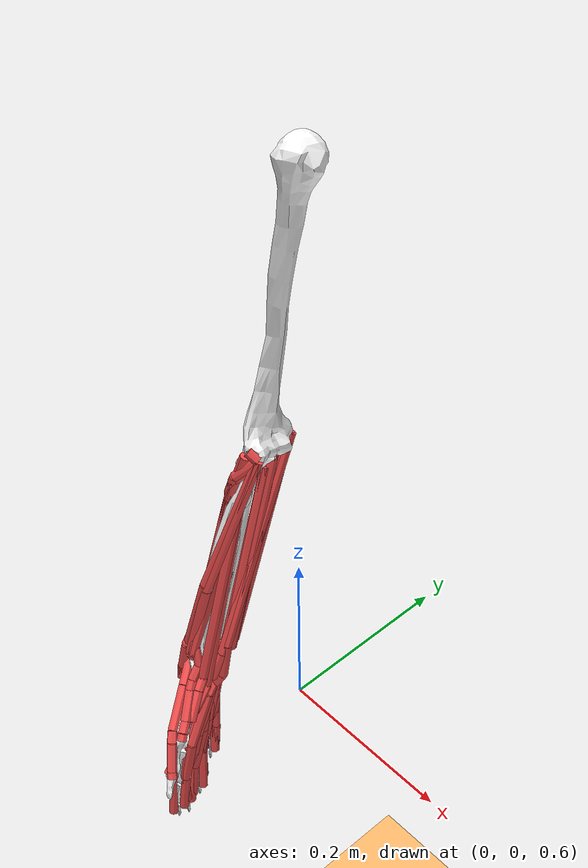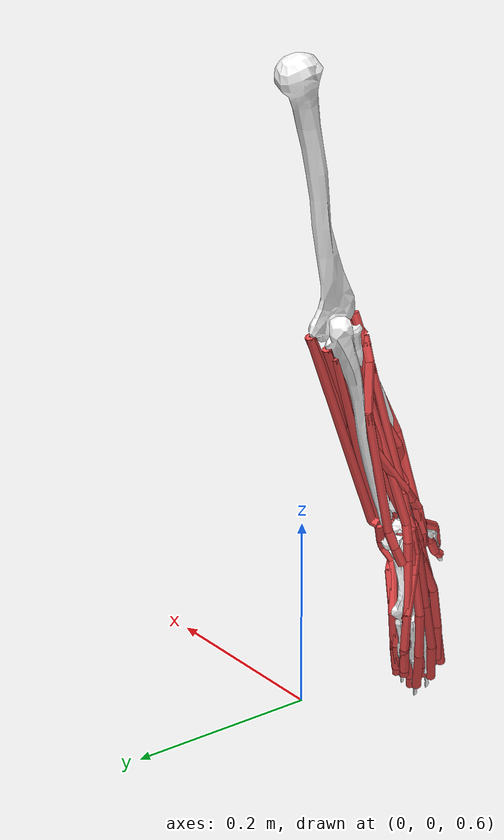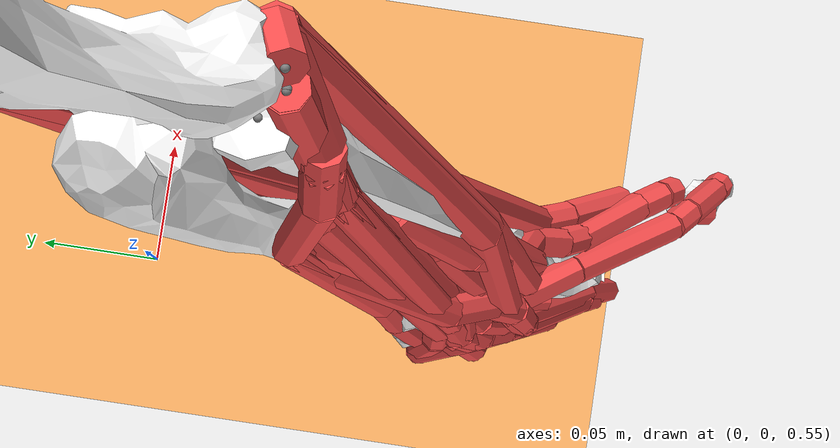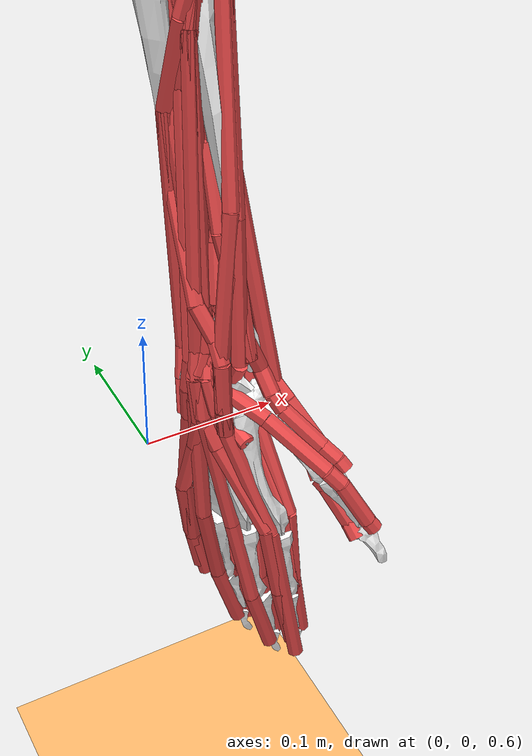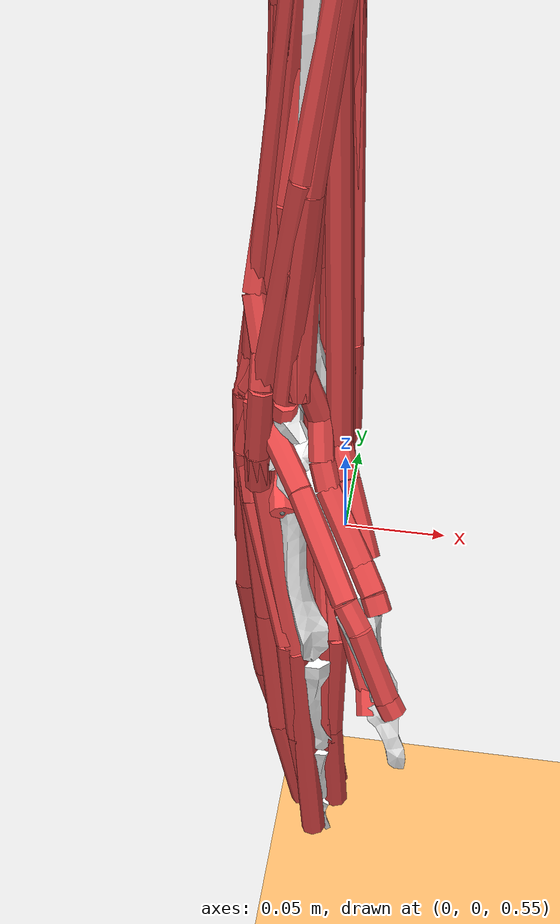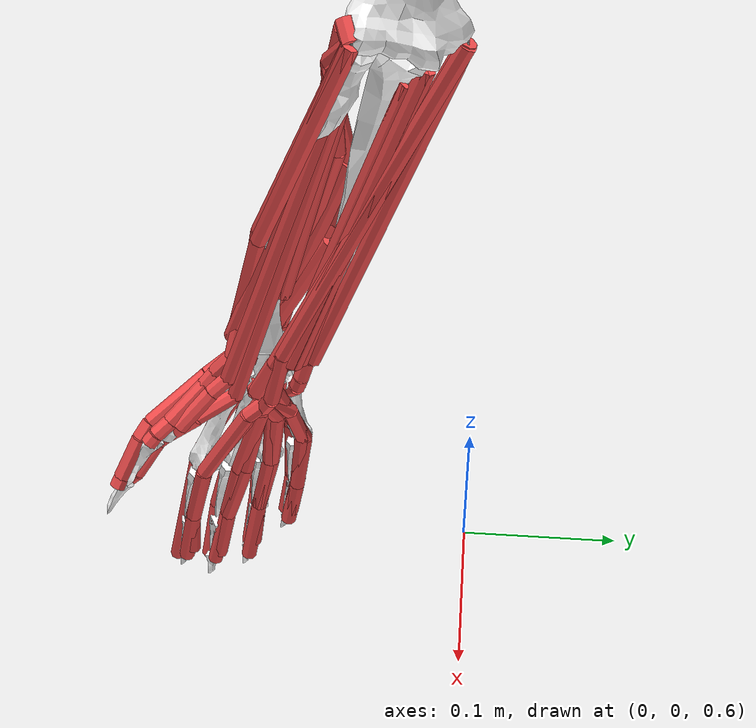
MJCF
<mujoco model="template">
  <!-- This model has been converted from an OpenSim model. Model conversion by MyoConverter https://github.com/MyoHub/myoconverter. This model is licensed under Apache 2.0. -->
  <!-- Credits from the original OpenSim model. Note! If the following has any license information, it applies to the original OpenSim model. Credits: Gonzalez, R.V., Buchanan, T.S., Delp, S.L. -->
  <!-- Note: inertiagrouprange="0 1" means that groups 0-1 will be used to infer masses/inertias, and groups 2-5 are
  only for visualisation (e.g. wrapping objects) !-->
  <compiler inertiafromgeom="auto" angle="radian" balanceinertia="true" boundmass="0.001" boundinertia="0.001" inertiagrouprange="0 1">
    <lengthrange inttotal="50" useexisting="true"/>
  </compiler>
  <option collision="predefined"/>
  <visual>
    <scale framelength="0.5" framewidth="0.01"/>
  </visual>
  <default>
    <joint limited="true" damping="0.05" armature="0.00001" stiffness="0"/>
    <geom rgba="0.8 0.6 .4 1" margin="0.001"/>
    <site size="0.001"/>
    <tendon width="0.005" rgba=".95 .3 .3 1" limited="false"/>
    <default class="muscle">
      <muscle ctrllimited="true" ctrlrange="0 1" scale="200"/>
    </default>
    <default class="motor">
      <general gainprm="5 0 0 0 0 0 0 0 0 0"/>
    </default>
  </default>
  <option timestep="0.002"/>
  <!-- nuser_jnt=1, the parameter is used to store default value of the joint, and nkey=1 to store keyframe with
   default joint positions set !-->
  <size njmax="1000" nconmax="400" nuser_jnt="1" nkey="1"/>
  <worldbody>
    <!-- The converter script assumes a body named 'ground' exists as a child element of worldbody -->
    <body name="ground" euler="1.571 0 0">
      <geom name="ground-plane" pos="0 0 0" euler="-1.571 0 0" size="10 10 0.125" type="plane" rgba="1.0 0.7 0.4 1.0" condim="3"/>
      <geom name="ground_geom_1" type="mesh" pos="0 1.274 0" euler="-0 0 -0" mesh="ground_geom_1_humerus" rgba="1 1 1 1" group="0"/>
      <site name="FCR_FCR-P1" pos="0.0063899999999999998 0.99639 0.013129999999999999"/>
      <site name="FCU_FCU-P1" pos="0.0046299999999999996 0.99631999999999998 0.013180000000000001"/>
      <site name="ECU_pre-surgery_ECU_pre-surgery-P1" pos="0.022679999999999999 1.00596 0.066790000000000002"/>
      <site name="ECU_post-surgery_ECU_post-surgery-P1" pos="0.022679999999999999 1.00596 0.066790000000000002"/>
      <site name="EDM_EDM-P1" pos="0.02257 1.0060800000000001 0.066830000000000001"/>
      <site name="ECRB_ECRB-P1" pos="0.022540000000000001 1.00587 0.066790000000000002"/>
      <site name="ECRL_ECRL-P1" pos="0.01337 1.0128900000000001 0.070690000000000003"/>
      <site name="ECRL_ECRL-P2" pos="0.02239 1.00566 0.066790000000000002"/>
      <site name="FDSI_FDSI-P1" pos="0.0035000000000000001 0.97945000000000004 0.032259999999999997"/>
      <site name="FDSM_FDSM-P1" pos="0.0035000000000000001 0.97945000000000004 0.032259999999999997"/>
      <site name="FDSR_FDSR-P1" pos="0.0035000000000000001 0.97945000000000004 0.032259999999999997"/>
      <site name="FDSL_FDSL-P1" pos="0.0035000000000000001 0.97945000000000004 0.032259999999999997"/>
      <site name="EDCL_EDCL-P1" pos="0.01056 1.0061100000000001 0.07127"/>
      <site name="EDCR_EDCR-P1" pos="0.010109999999999999 1.0061100000000001 0.07127"/>
      <site name="EDCM_EDCM-P1" pos="0.010109999999999999 1.0061100000000001 0.07127"/>
      <site name="EDCI_EDCI-P1" pos="0.010109999999999999 1.0061100000000001 0.07127"/>
      <site name="PL_PL-P1" pos="0.0046800000000000001 0.99702000000000002 0.01316"/>
    </body>
    <light directional="true"/>
    <body name="ulna" pos="0.0127 -0.0389 1" euler="1.571 0 0">
      <inertial mass="0" pos="0 0 0"/>
      <geom name="ulna_geom_1" type="mesh" mesh="ulna_geom_1_ulna" rgba="1 1 1 1" group="0"/>
      <joint name="elbow_flexion" range="0 2.269" limited="false" user="0.0" ref="0" axis="0.226 0.191 0.9552" type="hinge" damping="0" stiffness="0"/>
      <body name="radius" pos="-0.0065 -0.008 0.027" euler="-0 0 0">
        <inertial mass="0" pos="0 0 0"/>
        <geom name="radius_geom_1" type="mesh" mesh="radius_geom_1_radius" rgba="1 1 1 1" group="0"/>
        <joint name="pro_sup" range="-1.571 1.571" limited="false" user="0.0" ref="0" axis="0.0564 0.9836 -0.1714" type="hinge"/>
        <body name="rotaxis" pos="-0.0085 -0.2313 0.0561" euler="-0.2618 0.3927 2.776e-17">
          <inertial mass="0" pos="0 0 0"/>
          <body name="auxprfem" pos="-0.001 0.009 0" euler="-0 0 0">
            <inertial mass="0" pos="0 0 0"/>
            <joint name="rotaxis_auxprfem_r3" range="-1e+05 1e+05" limited="false" user="0.0" ref="0" axis="0 0 1" type="hinge"/>
            <body name="auxprrud" pos="0 0 0" euler="-0 0 0">
              <inertial mass="0" pos="0 0 0"/>
              <joint name="auxprfem-auxprrud_coord" range="-0.4363 0.6109" limited="false" user="0.0" ref="0" axis="1 0 0" type="hinge"/>
              <body name="auxdrfem" pos="0.001 -0.02 0" euler="-0 0 0">
                <inertial mass="0" pos="0 0 0"/>
                <joint name="auxprrud_auxdrfem_r3" range="-1e+05 1e+05" limited="false" user="0.0" ref="0" axis="0 0 1" type="hinge"/>
                <body name="auxdrrud" pos="0 0 0" euler="-0 0 0">
                  <inertial mass="0" pos="0 0 0"/>
                  <joint name="auxdrfem_auxdrrud_r1" range="-1e+05 1e+05" limited="false" user="0.0" ref="0" axis="1 0 0" type="hinge"/>
                  <body name="trapezium" pos="0.0035 -0.0035 0.02" euler="-0.2618 0 0">
                    <inertial mass="0" pos="0 0 0"/>
                    <geom name="trapezium_geom_1" type="mesh" mesh="trapezium_geom_1_r_trpzm" rgba="1 1 1 1" group="0"/>
                    <site name="APL_APL-P7" pos="0.0072199999999999999 0.0090600000000000003 0.01082"/>
                    <site name="EPB_EPB-P6" pos="-0.00077999999999999999 0.0045799999999999999 0.014749999999999999"/>
                  </body>
                  <body name="trapezoid" pos="-0.0015 -0.0044 0.0134" euler="0.3491 -0.1745 0">
                    <inertial mass="0" pos="0 0 0"/>
                    <geom name="trapezoid_geom_1" type="mesh" mesh="trapezoid_geom_1_r_trpzd" rgba="1 1 1 1" group="0"/>
                    <site name="FCR_FCR-P3" pos="0.013950000000000001 -0.0011999999999999999 -0.0067000000000000002"/>
                    <site name="ECU_post-surgery_ECU_post-surgery-P9" pos="-0.01575 0.0030200000000000001 0.00216"/>
                    <site name="ECRB_ECRB-P4" pos="-0.015980000000000001 0.0025699999999999998 0.00197"/>
                  </body>
                  <body name="capitate" pos="-0.0155 -0.0018 -0.0055" euler="0.1745 0 0">
                    <inertial mass="0" pos="0 0 0"/>
                    <geom name="capitate_geom_1" type="mesh" mesh="capitate_geom_1_r_cap" rgba="1 1 1 1" group="0"/>
                    <body name="FDSI_FDSI-P4" pos="0 0 0">
                      <geom size="0.0005 0.0005 0.0005" rgba="0.0 0.0 1.0 0.0" contype="2" conaffinity="2"/>
                      <joint name="FDSI_FDSI-P4_x" type="slide" axis="1 0 0" range="0.02244 0.02944"/>
                      <joint name="FDSI_FDSI-P4_y" type="slide" axis="0 1 0" range="-0.01143 0.01397"/>
                      <joint name="FDSI_FDSI-P4_z" type="slide" axis="0 0 1" range="0.00139 0.00869"/>
                      <site name="FDSI_FDSI-P4"/>
                    </body>
                    <body name="FDSI_FDSI-P5" pos="0 0 0">
                      <geom size="0.0005 0.0005 0.0005" rgba="0.0 0.0 1.0 0.0" contype="2" conaffinity="2"/>
                      <joint name="FDSI_FDSI-P5_x" type="slide" axis="1 0 0" range="0.02703 0.02944"/>
                      <joint name="FDSI_FDSI-P5_y" type="slide" axis="0 1 0" range="-0.01143 0.00411"/>
                      <joint name="FDSI_FDSI-P5_z" type="slide" axis="0 0 1" range="0.00444 0.00869"/>
                      <site name="FDSI_FDSI-P5"/>
                    </body>
                    <site name="FDSI_FDSI-P6" pos="0.029440000000000001 -0.011429999999999999 0.0086899999999999998"/>
                    <body name="FDSM_FDSM-P4" pos="0 0 0">
                      <geom size="0.0005 0.0005 0.0005" rgba="0.0 0.0 1.0 0.0" contype="2" conaffinity="2"/>
                      <joint name="FDSM_FDSM-P4_x" type="slide" axis="1 0 0" range="0.02277 0.03"/>
                      <joint name="FDSM_FDSM-P4_y" type="slide" axis="0 1 0" range="-0.0118 0.01364"/>
                      <joint name="FDSM_FDSM-P4_z" type="slide" axis="0 0 1" range="0.00172 0.0084"/>
                      <site name="FDSM_FDSM-P4"/>
                    </body>
                    <body name="FDSM_FDSM-P5" pos="0 0 0">
                      <geom size="0.0005 0.0005 0.0005" rgba="0.0 0.0 1.0 0.0" contype="2" conaffinity="2"/>
                      <joint name="FDSM_FDSM-P5_x" type="slide" axis="1 0 0" range="0.0269 0.03"/>
                      <joint name="FDSM_FDSM-P5_y" type="slide" axis="0 1 0" range="-0.0118 0.0054"/>
                      <joint name="FDSM_FDSM-P5_z" type="slide" axis="0 0 1" range="0.0037 0.0084"/>
                      <site name="FDSM_FDSM-P5"/>
                    </body>
                    <site name="FDSM_FDSM-P6" pos="0.029999999999999999 -0.0118 0.0083999999999999995"/>
                    <body name="FDSR_FDSR-P4" pos="0 0 0">
                      <geom size="0.0005 0.0005 0.0005" rgba="0.0 0.0 1.0 0.0" contype="2" conaffinity="2"/>
                      <joint name="FDSR_FDSR-P4_x" type="slide" axis="1 0 0" range="0.02189 0.0289"/>
                      <joint name="FDSR_FDSR-P4_y" type="slide" axis="0 1 0" range="-0.0155 0.01306"/>
                      <joint name="FDSR_FDSR-P4_z" type="slide" axis="0 0 1" range="0.00048 0.0073"/>
                      <site name="FDSR_FDSR-P4"/>
                    </body>
                    <body name="FDSR_FDSR-P5" pos="0 0 0">
                      <geom size="0.0005 0.0005 0.0005" rgba="0.0 0.0 1.0 0.0" contype="2" conaffinity="2"/>
                      <joint name="FDSR_FDSR-P5_x" type="slide" axis="1 0 0" range="0.02545 0.0289"/>
                      <joint name="FDSR_FDSR-P5_y" type="slide" axis="0 1 0" range="-0.0155 0.00479"/>
                      <joint name="FDSR_FDSR-P5_z" type="slide" axis="0 0 1" range="0.0023 0.0073"/>
                      <site name="FDSR_FDSR-P5"/>
                    </body>
                    <site name="FDSR_FDSR-P6" pos="0.028899999999999999 -0.0155 0.0073000000000000001"/>
                    <body name="FDSL_FDSL-P4" pos="0 0 0">
                      <geom size="0.0005 0.0005 0.0005" rgba="0.0 0.0 1.0 0.0" contype="2" conaffinity="2"/>
                      <joint name="FDSL_FDSL-P4_x" type="slide" axis="1 0 0" range="0.02201 0.0268"/>
                      <joint name="FDSL_FDSL-P4_y" type="slide" axis="0 1 0" range="-0.0129 0.01258"/>
                      <joint name="FDSL_FDSL-P4_z" type="slide" axis="0 0 1" range="-0.00027 0.0061"/>
                      <site name="FDSL_FDSL-P4"/>
                    </body>
                    <body name="FDSL_FDSL-P5" pos="0 0 0">
                      <geom size="0.0005 0.0005 0.0005" rgba="0.0 0.0 1.0 0.0" contype="2" conaffinity="2"/>
                      <joint name="FDSL_FDSL-P5_x" type="slide" axis="1 0 0" range="0.0255 0.0268"/>
                      <joint name="FDSL_FDSL-P5_y" type="slide" axis="0 1 0" range="-0.0129 0.0021"/>
                      <joint name="FDSL_FDSL-P5_z" type="slide" axis="0 0 1" range="0.0025 0.0061"/>
                      <site name="FDSL_FDSL-P5"/>
                    </body>
                    <site name="FDSL_FDSL-P6" pos="0.026800000000000001 -0.0129 0.0061000000000000004"/>
                    <site name="FDPI_FDPI-P4" pos="0.022689999999999998 0.011169999999999999 0.00347"/>
                    <site name="FDPI_FDPI-P5" pos="0.024989999999999998 0.00064999999999999997 0.0058900000000000003"/>
                    <site name="FDPM_FDPM-P4" pos="0.021250000000000002 0.01055 0.0015399999999999999"/>
                    <site name="FDPM_FDPM-P5" pos="0.023460000000000002 0.00125 0.0038400000000000001"/>
                    <site name="FDPR_FDPR-P4" pos="0.023800000000000002 0.011169999999999999 -0.00097000000000000005"/>
                    <site name="FDPR_FDPR-P5" pos="0.028289999999999999 0.00175 0.0047299999999999998"/>
                    <site name="FDPL_FDPL-P4" pos="0.024240000000000001 0.012330000000000001 0.00080000000000000004"/>
                    <site name="FDPL_FDPL-P5" pos="0.028289999999999999 0.00175 0.0047299999999999998"/>
                    <site name="EDCL_EDCL-P6" pos="-0.00192 -0.011509999999999999 0.00084000000000000003"/>
                    <site name="EDCI_EDCI-P6" pos="-0.0019599999999999999 -0.0065500000000000003 0.00232"/>
                    <site name="PL_PL-P3" pos="0.036889999999999999 0.0013500000000000001 0.0073200000000000001"/>
                  </body>
                  <body name="hamate" pos="-0.006 -0.005 -0.0175" euler="-0.2094 0 0">
                    <inertial mass="0" pos="0 0 0"/>
                    <geom name="hamate_geom_1" type="mesh" mesh="hamate_geom_1_r_ham" rgba="1 1 1 1" group="0"/>
                    <site name="FCU_FCU-P4" pos="0.019009999999999999 0.0109 0.0026099999999999999"/>
                    <site name="FCU_FCU-P5" pos="0.01899 0.0023999999999999998 0.0011999999999999999"/>
                  </body>
                  <body name="carp_metacarp" pos="0 0 0" euler="-0 0 0">
                    <inertial mass="0" pos="0 0 0"/>
                    <body name="metacarpal2" pos="-0.0047 -0.0095 -0.005" euler="0.1745 0.2618 0">
                      <inertial mass="0" pos="0 0 0"/>
                      <geom name="metacarpal2_geom_1" type="mesh" mesh="metacarpal2_geom_1_fingers1" rgba="1 1 1 1" group="0"/>
                      <body name="Iphalanx1" pos="-0.002402 -0.0685 0.045" euler="-0 0 0">
                        <inertial mass="0" pos="0 0 0"/>
                        <geom name="Iphalanx1_geom_1" type="mesh" mesh="Iphalanx1_geom_1_fingers2" rgba="1 1 1 1" group="0"/>
                        <joint name="MCP2_lateral" range="-0.3491 0.3491" limited="false" user="0.0" ref="0" axis="1 0 0" type="hinge"/>
                        <joint name="MCP2_flex" range="-0.1745 1.571" limited="false" user="0.0" ref="0" axis="0 0 1" type="hinge"/>
                        <body name="Iphalanx2" pos="0.0005 -0.04826 0.00799" euler="-0 0 0">
                          <inertial mass="0" pos="0 0 0"/>
                          <geom name="Iphalanx2_geom_1" type="mesh" mesh="Iphalanx2_geom_1_fingers3" rgba="1 1 1 1" group="0"/>
                          <joint name="PIP_flex" range="-0.08727 1.571" limited="false" user="0.0" ref="0" axis="0 0 1" type="hinge"/>
                          <body name="Iphalanx3" pos="0.00193 -0.03277 0.00472" euler="-0 0 0">
                            <inertial mass="0" pos="0 0 0"/>
                            <geom name="Iphalanx3_geom_1" type="mesh" mesh="Iphalanx3_geom_1_fingers4" rgba="1 1 1 1" group="0"/>
                            <joint name="DIP_flex" range="-0.08727 1.571" limited="false" user="0.0" ref="0" axis="0 0 1" type="hinge"/>
                            <site name="FDSI_FDSI-P10" pos="0.0058100000000000001 -0.0058999999999999999 0.00263"/>
                            <site name="EDCI_EDCI-P10" pos="-0.0029099999999999998 -0.01043 6.9999999999999994e-05"/>
                            <site name="EIP_EIP-P6" pos="-0.0045199999999999997 -0.018200000000000001 0.00396"/>
                          </body>
                          <site name="FDPI_FDPI-P9" pos="0.0094999999999999998 -0.030280000000000001 0.0034299999999999999"/>
                        </body>
                        <site name="FDSI_FDSI-P9" pos="0.00596 -0.046240000000000003 0.0088299999999999993"/>
                        <site name="FDPI_FDPI-P8" pos="0.0049399999999999999 -0.050599999999999999 0.0091400000000000006"/>
                        <site name="EDCI_EDCI-P9" pos="-0.0065799999999999999 -0.048520000000000001 0.0044000000000000003"/>
                      </body>
                      <site name="FCR_FCR-P4" pos="0.0059199999999999999 0.0026900000000000001 0.01328"/>
                      <body name="ECRL_ECRL-P5" pos="0 0 0">
                        <geom size="0.0005 0.0005 0.0005" rgba="0.0 0.0 1.0 0.0" contype="2" conaffinity="2"/>
                        <joint name="ECRL_ECRL-P5_x" type="slide" axis="1 0 0" range="-0.01349 -0.01108"/>
                        <joint name="ECRL_ECRL-P5_y" type="slide" axis="0 1 0" range="-0.01106 0.01118"/>
                        <joint name="ECRL_ECRL-P5_z" type="slide" axis="0 0 1" range="0.02204 0.02568"/>
                        <site name="ECRL_ECRL-P5"/>
                      </body>
                      <site name="ECRL_ECRL-P6" pos="-0.01108 -0.01106 0.025680000000000001"/>
                      <site name="FDSI_FDSI-P7" pos="0.012970000000000001 -0.014370000000000001 0.021829999999999999"/>
                      <site name="FDSI_FDSI-P8" pos="0.0054299999999999999 -0.066879999999999995 0.047280000000000003"/>
                      <site name="FDPI_FDPI-P6" pos="0.012999999999999999 -0.0047999999999999996 0.01072"/>
                      <site name="FDPI_FDPI-P7" pos="0.00363 -0.066619999999999999 0.044900000000000002"/>
                      <site name="EDCI_EDCI-P8" pos="-0.01225 -0.069260000000000002 0.040419999999999998"/>
                      <site name="EIP_EIP-P4" pos="-0.01312 0.0059500000000000004 0.0074999999999999997"/>
                      <site name="EIP_EIP-P5" pos="-0.01022 -0.071790000000000007 0.042930000000000003"/>
                    </body>
                    <body name="metacarpal3" pos="-0.0047 -0.0085 -0.005" euler="0.08727 0.1745 0.08727">
                      <inertial mass="0" pos="0 0 0"/>
                      <geom name="metacarpal3_geom_1" type="mesh" mesh="metacarpal3_geom_1_fingers8" rgba="1 1 1 1" group="0"/>
                      <body name="midfinger" pos="0 -0.003 0" euler="-0 0 0">
                        <inertial mass="0" pos="0 0 0"/>
                        <geom name="midfinger_geom_1" type="mesh" mesh="midfinger_geom_1_fingers6" rgba="1 1 1 1" group="0"/>
                        <geom name="midfinger_geom_2" type="mesh" mesh="midfinger_geom_2_fingers7" rgba="1 1 1 1" group="0"/>
                        <geom name="midfinger_geom_3" type="mesh" mesh="midfinger_geom_3_fingers5" rgba="1 1 1 1" group="0"/>
                        <site name="FDSM_FDSM-P9" pos="-0.00048000000000000001 -0.12515999999999999 0.018509999999999999"/>
                        <site name="FDSM_FDSM-P10" pos="0.00027999999999999998 -0.17254 0.024830000000000001"/>
                        <site name="FDPM_FDPM-P8" pos="0.00087000000000000001 -0.12590000000000001 0.018530000000000001"/>
                        <site name="FDPM_FDPM-P9" pos="0.00142 -0.16485 0.0224"/>
                        <site name="EDCM_EDCM-P8" pos="-0.013469999999999999 -0.13109000000000001 0.01966"/>
                        <site name="EDCM_EDCM-P9" pos="-0.0073699999999999998 -0.17491999999999999 0.025760000000000002"/>
                      </body>
                      <site name="ECU_post-surgery_ECU_post-surgery-P10" pos="-0.01502 -0.00464 0.01507"/>
                      <site name="ECRB_ECRB-P5" pos="-0.01528 -0.0050600000000000003 0.01554"/>
                      <site name="FDSM_FDSM-P7" pos="0.0144 -0.016320000000000001 0.01008"/>
                      <site name="FDSM_FDSM-P8" pos="0.0042900000000000004 -0.080119999999999997 0.015959999999999998"/>
                      <site name="FDSR_FDSR-P7" pos="0.0144 -0.0252 -0.00101"/>
                      <site name="FDPM_FDPM-P6" pos="0.011679999999999999 -0.00745 0.0075500000000000003"/>
                      <site name="FDPM_FDPM-P7" pos="0.0076499999999999997 -0.075980000000000006 0.012880000000000001"/>
                      <site name="FDPR_FDPR-P6" pos="0.012630000000000001 -0.015299999999999999 0.00166"/>
                      <site name="EDCL_EDCL-P7" pos="-0.010959999999999999 -0.024719999999999999 -0.01035"/>
                      <site name="EDCR_EDCR-P6" pos="-0.0090299999999999998 0.0083700000000000007 -0.0074099999999999999"/>
                      <body name="EDCM_EDCM-P6" pos="-0.01348 0 0">
                        <geom size="0.0005 0.0005 0.0005" rgba="0.0 0.0 1.0 0.0" contype="2" conaffinity="2"/>
                        <joint name="EDCM_EDCM-P6_y" type="slide" axis="0 1 0" range="-0.07696 0.00659"/>
                        <joint name="EDCM_EDCM-P6_z" type="slide" axis="0 0 1" range="-0.00208 0.01108"/>
                        <site name="EDCM_EDCM-P6"/>
                      </body>
                      <site name="EDCM_EDCM-P7" pos="-0.013480000000000001 -0.076960000000000001 0.01108"/>
                      <site name="EDCI_EDCI-P7" pos="-0.01421 -0.018859999999999998 0.0077999999999999996"/>
                      <site name="PL_PL-P4" pos="0.0093200000000000002 -0.023769999999999999 0.0098099999999999993"/>
                    </body>
                    <body name="metacarpal4" pos="-0.0047 -0.008 -0.0033" euler="0.08727 0.1745 0.08727">
                      <inertial mass="0" pos="0 0 0"/>
                      <geom name="metacarpal4_geom_1" type="mesh" mesh="metacarpal4_geom_1_fingers12" rgba="1 1 1 1" group="0"/>
                      <body name="ringfinger" pos="0 -0.0025 0" euler="-0 0 0">
                        <inertial mass="0" pos="0 0 0"/>
                        <geom name="ringfinger_geom_1" type="mesh" mesh="ringfinger_geom_1_fingers10" rgba="1 1 1 1" group="0"/>
                        <geom name="ringfinger_geom_2" type="mesh" mesh="ringfinger_geom_2_fingers11" rgba="1 1 1 1" group="0"/>
                        <geom name="ringfinger_geom_3" type="mesh" mesh="ringfinger_geom_3_fingers9" rgba="1 1 1 1" group="0"/>
                        <site name="FDSR_FDSR-P9" pos="0.0033 -0.12454999999999999 -0.0044099999999999999"/>
                        <site name="FDSR_FDSR-P10" pos="0.0067200000000000003 -0.17283000000000001 0.0010200000000000001"/>
                        <site name="FDPR_FDPR-P8" pos="0.0028800000000000002 -0.12884999999999999 -0.0044000000000000003"/>
                        <site name="FDPR_FDPR-P9" pos="0.0060899999999999999 -0.15981000000000001 -0.0023"/>
                        <site name="EDCR_EDCR-P8" pos="-0.0088000000000000005 -0.12604000000000001 -0.0085900000000000004"/>
                        <site name="EDCR_EDCR-P9" pos="-0.00093000000000000005 -0.16986999999999999 -0.00249"/>
                      </body>
                      <site name="FDSR_FDSR-P8" pos="0.0080700000000000008 -0.076350000000000001 -0.00696"/>
                      <site name="FDSL_FDSL-P7" pos="0.014630000000000001 -0.024979999999999999 -0.011509999999999999"/>
                      <site name="FDPR_FDPR-P7" pos="0.0078799999999999999 -0.076649999999999996 -0.0055999999999999999"/>
                      <site name="FDPL_FDPL-P6" pos="0.01286 -0.015970000000000002 -0.0061700000000000001"/>
                      <site name="EDCR_EDCR-P7" pos="-0.013780000000000001 -0.076060000000000003 -0.01001"/>
                    </body>
                    <body name="metacarpal5" pos="-0.002 -0.01 0.0035" euler="0.08727 0.1745 0.08727">
                      <inertial mass="0" pos="0 0 0"/>
                      <geom name="metacarpal5_geom_1" type="mesh" mesh="metacarpal5_geom_1_fingers16" rgba="1 1 1 1" group="0"/>
                      <body name="littlefinger" pos="0 -0.002 0" euler="-0 0 0">
                        <inertial mass="0" pos="0 0 0"/>
                        <geom name="littlefinger_geom_1" type="mesh" mesh="littlefinger_geom_1_fingers14" rgba="1 1 1 1" group="0"/>
                        <geom name="littlefinger_geom_2" type="mesh" mesh="littlefinger_geom_2_fingers15" rgba="1 1 1 1" group="0"/>
                        <geom name="littlefinger_geom_3" type="mesh" mesh="littlefinger_geom_3_fingers13" rgba="1 1 1 1" group="0"/>
                        <site name="EDM_EDM-P8" pos="-0.00281 -0.10702 -0.037130000000000003"/>
                        <site name="EDM_EDM-P9" pos="-0.00027 -0.13242999999999999 -0.035700000000000003"/>
                        <site name="FDSL_FDSL-P9" pos="0.0073000000000000001 -0.10135 -0.035700000000000003"/>
                        <site name="FDSL_FDSL-P10" pos="0.0098300000000000002 -0.13986000000000001 -0.031150000000000001"/>
                        <site name="FDPL_FDPL-P8" pos="0.0086499999999999997 -0.10564 -0.034790000000000001"/>
                        <site name="FDPL_FDPL-P9" pos="0.0091999999999999998 -0.13216 -0.032689999999999997"/>
                        <site name="EDCL_EDCL-P9" pos="-0.0030300000000000001 -0.10372000000000001 -0.037650000000000003"/>
                        <site name="EDCL_EDCL-P10" pos="0.0012899999999999999 -0.13957 -0.033329999999999999"/>
                      </body>
                      <site name="FCU_FCU-P6" pos="0.0084499999999999992 -0.0091000000000000004 -0.019630000000000002"/>
                      <site name="ECU_pre-surgery_ECU_pre-surgery-P7" pos="-0.0045799999999999999 -0.0073400000000000002 -0.028479999999999998"/>
                      <site name="EDM_EDM-P6" pos="-0.0089499999999999996 -0.0054599999999999996 -0.022669999999999999"/>
                      <site name="EDM_EDM-P7" pos="-0.0070899999999999999 -0.063289999999999999 -0.03424"/>
                      <site name="FDSL_FDSL-P8" pos="0.0067400000000000003 -0.061519999999999998 -0.034700000000000002"/>
                      <site name="FDPL_FDPL-P7" pos="0.0065500000000000003 -0.063589999999999994 -0.036889999999999999"/>
                      <site name="EDCL_EDCL-P8" pos="-0.0080099999999999998 -0.063890000000000002 -0.03508"/>
                    </body>
                    <body name="thumb" pos="0.008 -0.0045 0.0219" euler="-0 0 0">
                      <inertial mass="0" pos="0 0 0"/>
                      <geom name="thumb_geom_1" type="mesh" mesh="thumb_geom_1_fingers17" rgba="1 1 1 1" group="0"/>
                      <geom name="thumb_geom_2" type="mesh" mesh="thumb_geom_2_fingers18" rgba="1 1 1 1" group="0"/>
                      <geom name="thumb_geom_3" type="mesh" mesh="thumb_geom_3_fingers19" rgba="1 1 1 1" group="0"/>
                      <joint name="thumb_abd" range="-0.7854 0.2618" limited="false" user="0.0" ref="0" axis="1 0 0" type="hinge"/>
                      <joint name="thumb_flex" range="-0.7854 1.571" limited="false" user="0.0" ref="0" axis="0.0564 0.9836 -0.1714" type="hinge"/>
                      <body name="FPL_FPL-P5" pos="0.00577 0 0">
                        <geom size="0.0005 0.0005 0.0005" rgba="0.0 0.0 1.0 0.0" contype="2" conaffinity="2"/>
                        <joint name="FPL_FPL-P5_y" type="slide" axis="0 1 0" range="-0.0177 0.01018"/>
                        <joint name="FPL_FPL-P5_z" type="slide" axis="0 0 1" range="-0.01528 0.0199"/>
                        <site name="FPL_FPL-P5"/>
                      </body>
                      <site name="FPL_FPL-P6" pos="0.0063 -0.0177 0.019900000000000001"/>
                      <site name="FPL_FPL-P7" pos="9.0000000000000006e-05 -0.041750000000000002 0.034459999999999998"/>
                      <site name="FPL_FPL-P8" pos="0.00080999999999999996 -0.045940000000000002 0.038769999999999999"/>
                      <site name="FPL_FPL-P9" pos="0.00577 -0.06923 0.049480000000000003"/>
                      <site name="FPL_FPL-P10" pos="0.0049300000000000004 -0.077759999999999996 0.055419999999999997"/>
                      <site name="APL_APL-P8" pos="0.0038400000000000001 0.0019599999999999999 0.01452"/>
                      <site name="APL_APL-P9" pos="0.0081600000000000006 -0.02324 0.03082"/>
                      <site name="EPB_EPB-P7" pos="-0.0038700000000000002 0.00011 0.016469999999999999"/>
                      <site name="EPB_EPB-P8" pos="0.0045199999999999997 -0.02214 0.035929999999999997"/>
                      <site name="EPB_EPB-P9" pos="0.0073000000000000001 -0.030120000000000001 0.044080000000000001"/>
                      <site name="EPB_EPB-P10" pos="0.0087100000000000007 -0.03603 0.048000000000000001"/>
                      <site name="EPL_EPL-P6" pos="-0.013299999999999999 -0.00263 0.01214"/>
                      <site name="EPL_EPL-P7" pos="-0.0035200000000000001 -0.031980000000000001 0.04462"/>
                      <site name="EPL_EPL-P8" pos="0.00080999999999999996 -0.041070000000000002 0.050709999999999998"/>
                      <site name="EPL_EPL-P9" pos="0.0096600000000000002 -0.066930000000000003 0.060220000000000003"/>
                      <site name="EPL_EPL-P10" pos="0.012279999999999999 -0.072819999999999996 0.062689999999999996"/>
                    </body>
                  </body>
                </body>
              </body>
              <body name="scaphoid" pos="-0.0035 -0.0025 0.009" euler="0.4014 0 0">
                <inertial mass="0" pos="0 0 0"/>
                <geom name="scaphoid_geom_1" type="mesh" mesh="scaphoid_geom_1_r_scaph" rgba="1 1 1 1" group="0"/>
                <site name="EDCL_EDCL-P5" pos="-0.01357 -0.0079000000000000008 -0.012409999999999999"/>
                <site name="EDCR_EDCR-P5" pos="-0.01286 -0.0041999999999999997 -0.01106"/>
                <site name="EDCM_EDCM-P5" pos="-0.011979999999999999 -0.00332 -0.012829999999999999"/>
                <site name="EDCI_EDCI-P5" pos="-0.01359 -0.0076099999999999996 -0.01108"/>
                <site name="EPL_EPL-P4" pos="-0.0080000000000000002 0.00038000000000000002 -0.0077400000000000004"/>
                <site name="EPL_EPL-P5" pos="-0.0083999999999999995 -0.0066299999999999996 0.0031900000000000001"/>
                <site name="EIP_EIP-P3" pos="-0.01119 -0.0044799999999999996 -0.0048300000000000001"/>
              </body>
              <body name="lunate" pos="-0.004 -0.0015 -0.007" euler="-0 0 0">
                <inertial mass="0" pos="0 0 0"/>
                <geom name="lunate_geom_1" type="mesh" mesh="lunate_geom_1_r_lun" rgba="1 1 1 1" group="0"/>
              </body>
              <body name="pisiform" pos="0.005 -0.015 -0.0201" euler="-0 0 0">
                <inertial mass="0" pos="0 0 0"/>
                <geom name="pisiform_geom_1" type="mesh" mesh="pisiform_geom_1_r_pis" rgba="1 1 1 1" group="0"/>
              </body>
              <body name="triquetrum" pos="-0.0055 -0.01 -0.021" euler="-0 0 0">
                <inertial mass="0" pos="0 0 0"/>
                <geom name="triquetrum_geom_1" type="mesh" mesh="triquetrum_geom_1_r_triq" rgba="1 1 1 1" group="0"/>
                <site name="ECU_pre-surgery_ECU_pre-surgery-P6" pos="-0.00093999999999999997 -0.0043600000000000002 -0.0044200000000000003"/>
                <site name="EDM_EDM-P5" pos="-0.0096500000000000006 -0.0046100000000000004 0.0073299999999999997"/>
              </body>
            </body>
          </body>
          <body name="imagine" pos="0 0 0" euler="-0 0 0">
            <inertial mass="0" pos="0 0 0"/>
            <joint name="deviation" range="-0.4363 0.6109" limited="false" user="0.0" ref="0" axis="1 0 0" type="hinge"/>
            <joint name="flexion" range="-1.222 1.222" limited="false" user="0.0" ref="0" axis="0 0 1" type="hinge"/>
          </body>
        </body>
        <site name="FCR_FCR-P2" pos="0.0095300000000000003 -0.21667 0.05024"/>
        <site name="ECU_pre-surgery_ECU_pre-surgery-P2" pos="-0.0023900000000000002 -0.010189999999999999 0.01329"/>
        <site name="ECU_pre-surgery_ECU_pre-surgery-P3" pos="-0.01094 -0.035459999999999998 0.01362"/>
        <site name="ECU_post-surgery_ECU_post-surgery-P2" pos="-0.0023900000000000002 -0.010189999999999999 0.01329"/>
        <site name="ECU_post-surgery_ECU_post-surgery-P3" pos="-0.01094 -0.035459999999999998 0.01362"/>
        <site name="ECU_post-surgery_ECU_post-surgery-P7" pos="-0.01789 -0.19788 0.064589999999999995"/>
        <site name="ECU_post-surgery_ECU_post-surgery-P8" pos="-0.01779 -0.20954 0.072340000000000002"/>
        <site name="EDM_EDM-P2" pos="-0.0052300000000000003 -0.018020000000000001 0.01357"/>
        <site name="EDM_EDM-P3" pos="-0.010749999999999999 -0.072819999999999996 0.012370000000000001"/>
        <site name="ECRB_ECRB-P2" pos="-0.0038400000000000001 -0.12479999999999999 0.054820000000000001"/>
        <site name="ECRB_ECRB-P3" pos="-0.017330000000000002 -0.20891999999999999 0.070400000000000004"/>
        <site name="ECRL_ECRL-P3" pos="-0.0013600000000000001 -0.12953000000000001 0.055320000000000001"/>
        <site name="ECRL_ECRL-P4" pos="-0.0083000000000000001 -0.21052000000000001 0.075200000000000003"/>
        <site name="FDSI_FDSI-P2" pos="0.01091 -0.21435999999999999 0.040480000000000002"/>
        <site name="FDSI_FDSI-P3" pos="0.00183 -0.21671000000000001 0.042529999999999998"/>
        <site name="FDSM_FDSM-P2" pos="0.01048 -0.21423 0.039780000000000003"/>
        <site name="FDSM_FDSM-P3" pos="0.0019 -0.2167 0.043799999999999999"/>
        <site name="FDSR_FDSR-P2" pos="0.010370000000000001 -0.21504000000000001 0.038620000000000002"/>
        <site name="FDSR_FDSR-P3" pos="-0.00036999999999999999 -0.21764 0.040899999999999999"/>
        <site name="FDSL_FDSL-P2" pos="0.01048 -0.21423 0.039780000000000003"/>
        <site name="FDSL_FDSL-P3" pos="0.001 -0.2177 0.041799999999999997"/>
        <site name="FDPI_FDPI-P2" pos="0.0079699999999999997 -0.21647 0.043950000000000003"/>
        <site name="FDPI_FDPI-P3" pos="0.0012999999999999999 -0.21659 0.046190000000000002"/>
        <site name="FDPM_FDPM-P2" pos="0.0043299999999999996 -0.21689 0.042700000000000002"/>
        <site name="FDPM_FDPM-P3" pos="-0.0015200000000000001 -0.21639 0.044450000000000003"/>
        <site name="FDPR_FDPR-P2" pos="0.0043800000000000002 -0.21834000000000001 0.037409999999999999"/>
        <site name="FDPR_FDPR-P3" pos="-0.0026099999999999999 -0.217 0.042860000000000002"/>
        <site name="FDPL_FDPL-P2" pos="0.0037699999999999999 -0.21886 0.035839999999999997"/>
        <site name="FDPL_FDPL-P3" pos="-0.0015 -0.217 0.043299999999999998"/>
        <site name="EDCL_EDCL-P2" pos="-0.0082000000000000007 -0.040039999999999999 0.01668"/>
        <site name="EDCL_EDCL-P3" pos="-0.019740000000000001 -0.18468999999999999 0.048070000000000002"/>
        <site name="EDCL_EDCL-P4" pos="-0.022110000000000001 -0.21096999999999999 0.05287"/>
        <site name="EDCR_EDCR-P2" pos="-0.0082000000000000007 -0.040039999999999999 0.01668"/>
        <site name="EDCR_EDCR-P3" pos="-0.017659999999999999 -0.18446000000000001 0.048980000000000003"/>
        <site name="EDCR_EDCR-P4" pos="-0.020209999999999999 -0.21054 0.055960000000000003"/>
        <site name="EDCM_EDCM-P2" pos="-0.0082000000000000007 -0.040039999999999999 0.01668"/>
        <site name="EDCM_EDCM-P3" pos="-0.016750000000000001 -0.18465999999999999 0.046820000000000001"/>
        <site name="EDCM_EDCM-P4" pos="-0.01933 -0.21054 0.051520000000000003"/>
        <site name="EDCI_EDCI-P2" pos="-0.0082000000000000007 -0.040039999999999999 0.01668"/>
        <site name="EDCI_EDCI-P3" pos="-0.022089999999999999 -0.18446000000000001 0.048980000000000003"/>
        <site name="EDCI_EDCI-P4" pos="-0.02376 -0.21054 0.0533"/>
        <site name="FPL_FPL-P1" pos="-0.0028400000000000001 -0.096049999999999996 0.029919999999999999"/>
        <site name="FPL_FPL-P2" pos="-0.00166 -0.13532 0.042569999999999997"/>
        <site name="FPL_FPL-P3" pos="-0.00036999999999999999 -0.16882 0.044389999999999999"/>
        <body name="FPL_FPL-P4" pos="0 0 0">
          <geom size="0.0005 0.0005 0.0005" rgba="0.0 0.0 1.0 0.0" contype="2" conaffinity="2"/>
          <joint name="FPL_FPL-P4_x" type="slide" axis="1 0 0" range="-0.00037 0.00345"/>
          <joint name="FPL_FPL-P4_y" type="slide" axis="0 1 0" range="-0.2143 -0.1688"/>
          <joint name="FPL_FPL-P4_z" type="slide" axis="0 0 1" range="0.04439 0.04621"/>
          <site name="FPL_FPL-P4"/>
        </body>
        <site name="APL_APL-P1" pos="-0.0049399999999999999 -0.096769999999999995 0.030040000000000001"/>
        <site name="APL_APL-P2" pos="-0.0089200000000000008 -0.13772000000000001 0.052549999999999999"/>
        <site name="APL_APL-P3" pos="-0.0066 -0.15947 0.06132"/>
        <site name="APL_APL-P4" pos="-0.0068199999999999997 -0.17731 0.064619999999999997"/>
        <site name="APL_APL-P5" pos="-0.00282 -0.20831 0.076069999999999999"/>
        <body name="APL_APL-P6" pos="0 0 0">
          <geom size="0.0005 0.0005 0.0005" rgba="0.0 0.0 1.0 0.0" contype="2" conaffinity="2"/>
          <joint name="APL_APL-P6_x" type="slide" axis="1 0 0" range="-0.00282 0.00117"/>
          <joint name="APL_APL-P6_y" type="slide" axis="0 1 0" range="-0.2151 -0.2083"/>
          <joint name="APL_APL-P6_z" type="slide" axis="0 0 1" range="0.07607 0.07845"/>
          <site name="APL_APL-P6"/>
        </body>
        <site name="EPB_EPB-P1" pos="-0.0029399999999999999 -0.13572999999999999 0.041959999999999997"/>
        <site name="EPB_EPB-P2" pos="-0.0070099999999999997 -0.14896000000000001 0.043869999999999999"/>
        <site name="EPB_EPB-P3" pos="-0.012829999999999999 -0.17881 0.058169999999999999"/>
        <site name="EPB_EPB-P4" pos="-0.00547 -0.19041 0.069610000000000005"/>
        <site name="EPB_EPB-P5" pos="0.0046899999999999997 -0.21768999999999999 0.075600000000000001"/>
        <site name="EPL_EPL-P2" pos="-0.01652 -0.16952 0.03814"/>
        <site name="EPL_EPL-P3" pos="-0.01762 -0.20537 0.052299999999999999"/>
        <site name="EIP_EIP-P2" pos="-0.016119999999999999 -0.20810999999999999 0.05228"/>
        <site name="PL_PL-P2" pos="0.011220000000000001 -0.20757999999999999 0.04487"/>
      </body>
      <site name="FCU_FCU-P2" pos="-0.0046499999999999996 -0.22771 0.055890000000000002"/>
      <site name="FCU_FCU-P3" pos="-0.013679999999999999 -0.22899 0.058049999999999997"/>
      <site name="ECU_pre-surgery_ECU_pre-surgery-P4" pos="-0.024570000000000002 -0.094219999999999998 0.033480000000000003"/>
      <site name="ECU_pre-surgery_ECU_pre-surgery-P5" pos="-0.02793 -0.23105999999999999 0.058729999999999997"/>
      <site name="ECU_post-surgery_ECU_post-surgery-P4" pos="-0.024570000000000002 -0.094219999999999998 0.033480000000000003"/>
      <site name="ECU_post-surgery_ECU_post-surgery-P5" pos="-0.024629999999999999 -0.13639999999999999 0.041590000000000002"/>
      <site name="ECU_post-surgery_ECU_post-surgery-P6" pos="-0.029530000000000001 -0.18933 0.078460000000000002"/>
      <site name="EDM_EDM-P4" pos="-0.032770000000000001 -0.22628000000000001 0.077689999999999995"/>
      <site name="FDPI_FDPI-P1" pos="-0.011299999999999999 -0.031570000000000001 0.0020799999999999998"/>
      <site name="FDPM_FDPM-P1" pos="-0.011299999999999999 -0.031570000000000001 0.0020799999999999998"/>
      <site name="FDPR_FDPR-P1" pos="-0.011299999999999999 -0.031570000000000001 0.0020799999999999998"/>
      <site name="FDPL_FDPL-P1" pos="-0.011299999999999999 -0.031570000000000001 0.0020799999999999998"/>
      <site name="EPL_EPL-P1" pos="-0.021270000000000001 -0.091600000000000001 0.032680000000000001"/>
      <site name="EIP_EIP-P1" pos="-0.019740000000000001 -0.14668 0.044490000000000002"/>
    </body>
  </worldbody>
  <asset>
    <texture type="skybox" builtin="gradient" rgb1="1 1 1" rgb2="0.6 0.8 1" width="256" height="256"/>
    <mesh name="ground_geom_1_humerus" file="Geometry\humerus.stl" scale="1 1 1"/>
    <mesh name="ulna_geom_1_ulna" file="Geometry\ulna.stl" scale="1 1 1"/>
    <mesh name="radius_geom_1_radius" file="Geometry\radius.stl" scale="1 1 1"/>
    <mesh name="trapezium_geom_1_r_trpzm" file="Geometry\r_trpzm.stl" scale="1 1 1"/>
    <mesh name="trapezoid_geom_1_r_trpzd" file="Geometry\r_trpzd.stl" scale="1 1 1"/>
    <mesh name="capitate_geom_1_r_cap" file="Geometry\r_cap.stl" scale="1 1 1"/>
    <mesh name="hamate_geom_1_r_ham" file="Geometry\r_ham.stl" scale="1 1 1"/>
    <mesh name="metacarpal2_geom_1_fingers1" file="Geometry\fingers1.stl" scale="1 1 1"/>
    <mesh name="Iphalanx1_geom_1_fingers2" file="Geometry\fingers2.stl" scale="1 1 1"/>
    <mesh name="Iphalanx2_geom_1_fingers3" file="Geometry\fingers3.stl" scale="1 1 1"/>
    <mesh name="Iphalanx3_geom_1_fingers4" file="Geometry\fingers4.stl" scale="1 1 1"/>
    <mesh name="metacarpal3_geom_1_fingers8" file="Geometry\fingers8.stl" scale="1 1 1"/>
    <mesh name="midfinger_geom_1_fingers6" file="Geometry\fingers6.stl" scale="1 1 1"/>
    <mesh name="midfinger_geom_2_fingers7" file="Geometry\fingers7.stl" scale="1 1 1"/>
    <mesh name="midfinger_geom_3_fingers5" file="Geometry\fingers5.stl" scale="1 1 1"/>
    <mesh name="metacarpal4_geom_1_fingers12" file="Geometry\fingers12.stl" scale="1 1 1"/>
    <mesh name="ringfinger_geom_1_fingers10" file="Geometry\fingers10.stl" scale="1 1 1"/>
    <mesh name="ringfinger_geom_2_fingers11" file="Geometry\fingers11.stl" scale="1 1 1"/>
    <mesh name="ringfinger_geom_3_fingers9" file="Geometry\fingers9.stl" scale="1 1 1"/>
    <mesh name="metacarpal5_geom_1_fingers16" file="Geometry\fingers16.stl" scale="1 1 1"/>
    <mesh name="littlefinger_geom_1_fingers14" file="Geometry\fingers14.stl" scale="1 1 1"/>
    <mesh name="littlefinger_geom_2_fingers15" file="Geometry\fingers15.stl" scale="1 1 1"/>
    <mesh name="littlefinger_geom_3_fingers13" file="Geometry\fingers13.stl" scale="1 1 1"/>
    <mesh name="thumb_geom_1_fingers17" file="Geometry\fingers17.stl" scale="1 1 1"/>
    <mesh name="thumb_geom_2_fingers18" file="Geometry\fingers18.stl" scale="1 1 1"/>
    <mesh name="thumb_geom_3_fingers19" file="Geometry\fingers19.stl" scale="1 1 1"/>
    <mesh name="scaphoid_geom_1_r_scaph" file="Geometry\r_scaph.stl" scale="1 1 1"/>
    <mesh name="lunate_geom_1_r_lun" file="Geometry\r_lun.stl" scale="1 1 1"/>
    <mesh name="pisiform_geom_1_r_pis" file="Geometry\r_pis.stl" scale="1 1 1"/>
    <mesh name="triquetrum_geom_1_r_triq" file="Geometry\r_triq.stl" scale="1 1 1"/>
  </asset>
  <tendon>
    <!-- Leave this comment here to make 'tendon' element pretty printed !-->
    <spatial name="FCR_tendon">
      <site site="FCR_FCR-P1"/>
      <site site="FCR_FCR-P2"/>
      <site site="FCR_FCR-P3"/>
      <site site="FCR_FCR-P4"/>
    </spatial>
    <spatial name="FCU_tendon">
      <site site="FCU_FCU-P1"/>
      <site site="FCU_FCU-P2"/>
      <site site="FCU_FCU-P3"/>
      <site site="FCU_FCU-P4"/>
      <site site="FCU_FCU-P5"/>
      <site site="FCU_FCU-P6"/>
    </spatial>
    <spatial name="ECU_pre-surgery_tendon">
      <site site="ECU_pre-surgery_ECU_pre-surgery-P1"/>
      <site site="ECU_pre-surgery_ECU_pre-surgery-P2"/>
      <site site="ECU_pre-surgery_ECU_pre-surgery-P3"/>
      <site site="ECU_pre-surgery_ECU_pre-surgery-P4"/>
      <site site="ECU_pre-surgery_ECU_pre-surgery-P5"/>
      <site site="ECU_pre-surgery_ECU_pre-surgery-P6"/>
      <site site="ECU_pre-surgery_ECU_pre-surgery-P7"/>
    </spatial>
    <spatial name="ECU_post-surgery_tendon">
      <site site="ECU_post-surgery_ECU_post-surgery-P1"/>
      <site site="ECU_post-surgery_ECU_post-surgery-P2"/>
      <site site="ECU_post-surgery_ECU_post-surgery-P3"/>
      <site site="ECU_post-surgery_ECU_post-surgery-P4"/>
      <site site="ECU_post-surgery_ECU_post-surgery-P5"/>
      <site site="ECU_post-surgery_ECU_post-surgery-P6"/>
      <site site="ECU_post-surgery_ECU_post-surgery-P7"/>
      <site site="ECU_post-surgery_ECU_post-surgery-P8"/>
      <site site="ECU_post-surgery_ECU_post-surgery-P9"/>
      <site site="ECU_post-surgery_ECU_post-surgery-P10"/>
    </spatial>
    <spatial name="EDM_tendon">
      <site site="EDM_EDM-P1"/>
      <site site="EDM_EDM-P2"/>
      <site site="EDM_EDM-P3"/>
      <site site="EDM_EDM-P4"/>
      <site site="EDM_EDM-P5"/>
      <site site="EDM_EDM-P6"/>
      <site site="EDM_EDM-P7"/>
      <site site="EDM_EDM-P8"/>
      <site site="EDM_EDM-P9"/>
    </spatial>
    <spatial name="ECRB_tendon">
      <site site="ECRB_ECRB-P1"/>
      <site site="ECRB_ECRB-P2"/>
      <site site="ECRB_ECRB-P3"/>
      <site site="ECRB_ECRB-P4"/>
      <site site="ECRB_ECRB-P5"/>
    </spatial>
    <spatial name="ECRL_tendon">
      <site site="ECRL_ECRL-P1"/>
      <site site="ECRL_ECRL-P2"/>
      <site site="ECRL_ECRL-P3"/>
      <site site="ECRL_ECRL-P4"/>
      <site site="ECRL_ECRL-P5"/>
      <site site="ECRL_ECRL-P6"/>
    </spatial>
    <spatial name="FDSI_tendon">
      <site site="FDSI_FDSI-P1"/>
      <site site="FDSI_FDSI-P2"/>
      <site site="FDSI_FDSI-P3"/>
      <site site="FDSI_FDSI-P4"/>
      <site site="FDSI_FDSI-P5"/>
      <site site="FDSI_FDSI-P6"/>
      <site site="FDSI_FDSI-P7"/>
      <site site="FDSI_FDSI-P8"/>
      <site site="FDSI_FDSI-P9"/>
      <site site="FDSI_FDSI-P10"/>
    </spatial>
    <spatial name="FDSM_tendon">
      <site site="FDSM_FDSM-P1"/>
      <site site="FDSM_FDSM-P2"/>
      <site site="FDSM_FDSM-P3"/>
      <site site="FDSM_FDSM-P4"/>
      <site site="FDSM_FDSM-P5"/>
      <site site="FDSM_FDSM-P6"/>
      <site site="FDSM_FDSM-P7"/>
      <site site="FDSM_FDSM-P8"/>
      <site site="FDSM_FDSM-P9"/>
      <site site="FDSM_FDSM-P10"/>
    </spatial>
    <spatial name="FDSR_tendon">
      <site site="FDSR_FDSR-P1"/>
      <site site="FDSR_FDSR-P2"/>
      <site site="FDSR_FDSR-P3"/>
      <site site="FDSR_FDSR-P4"/>
      <site site="FDSR_FDSR-P5"/>
      <site site="FDSR_FDSR-P6"/>
      <site site="FDSR_FDSR-P7"/>
      <site site="FDSR_FDSR-P8"/>
      <site site="FDSR_FDSR-P9"/>
      <site site="FDSR_FDSR-P10"/>
    </spatial>
    <spatial name="FDSL_tendon">
      <site site="FDSL_FDSL-P1"/>
      <site site="FDSL_FDSL-P2"/>
      <site site="FDSL_FDSL-P3"/>
      <site site="FDSL_FDSL-P4"/>
      <site site="FDSL_FDSL-P5"/>
      <site site="FDSL_FDSL-P6"/>
      <site site="FDSL_FDSL-P7"/>
      <site site="FDSL_FDSL-P8"/>
      <site site="FDSL_FDSL-P9"/>
      <site site="FDSL_FDSL-P10"/>
    </spatial>
    <spatial name="FDPI_tendon">
      <site site="FDPI_FDPI-P1"/>
      <site site="FDPI_FDPI-P2"/>
      <site site="FDPI_FDPI-P3"/>
      <site site="FDPI_FDPI-P4"/>
      <site site="FDPI_FDPI-P5"/>
      <site site="FDPI_FDPI-P6"/>
      <site site="FDPI_FDPI-P7"/>
      <site site="FDPI_FDPI-P8"/>
      <site site="FDPI_FDPI-P9"/>
    </spatial>
    <spatial name="FDPM_tendon">
      <site site="FDPM_FDPM-P1"/>
      <site site="FDPM_FDPM-P2"/>
      <site site="FDPM_FDPM-P3"/>
      <site site="FDPM_FDPM-P4"/>
      <site site="FDPM_FDPM-P5"/>
      <site site="FDPM_FDPM-P6"/>
      <site site="FDPM_FDPM-P7"/>
      <site site="FDPM_FDPM-P8"/>
      <site site="FDPM_FDPM-P9"/>
    </spatial>
    <spatial name="FDPR_tendon">
      <site site="FDPR_FDPR-P1"/>
      <site site="FDPR_FDPR-P2"/>
      <site site="FDPR_FDPR-P3"/>
      <site site="FDPR_FDPR-P4"/>
      <site site="FDPR_FDPR-P5"/>
      <site site="FDPR_FDPR-P6"/>
      <site site="FDPR_FDPR-P7"/>
      <site site="FDPR_FDPR-P8"/>
      <site site="FDPR_FDPR-P9"/>
    </spatial>
    <spatial name="FDPL_tendon">
      <site site="FDPL_FDPL-P1"/>
      <site site="FDPL_FDPL-P2"/>
      <site site="FDPL_FDPL-P3"/>
      <site site="FDPL_FDPL-P4"/>
      <site site="FDPL_FDPL-P5"/>
      <site site="FDPL_FDPL-P6"/>
      <site site="FDPL_FDPL-P7"/>
      <site site="FDPL_FDPL-P8"/>
      <site site="FDPL_FDPL-P9"/>
    </spatial>
    <spatial name="EDCL_tendon">
      <site site="EDCL_EDCL-P1"/>
      <site site="EDCL_EDCL-P2"/>
      <site site="EDCL_EDCL-P3"/>
      <site site="EDCL_EDCL-P4"/>
      <site site="EDCL_EDCL-P5"/>
      <site site="EDCL_EDCL-P6"/>
      <site site="EDCL_EDCL-P7"/>
      <site site="EDCL_EDCL-P8"/>
      <site site="EDCL_EDCL-P9"/>
      <site site="EDCL_EDCL-P10"/>
    </spatial>
    <spatial name="EDCR_tendon">
      <site site="EDCR_EDCR-P1"/>
      <site site="EDCR_EDCR-P2"/>
      <site site="EDCR_EDCR-P3"/>
      <site site="EDCR_EDCR-P4"/>
      <site site="EDCR_EDCR-P5"/>
      <site site="EDCR_EDCR-P6"/>
      <site site="EDCR_EDCR-P7"/>
      <site site="EDCR_EDCR-P8"/>
      <site site="EDCR_EDCR-P9"/>
    </spatial>
    <spatial name="EDCM_tendon">
      <site site="EDCM_EDCM-P1"/>
      <site site="EDCM_EDCM-P2"/>
      <site site="EDCM_EDCM-P3"/>
      <site site="EDCM_EDCM-P4"/>
      <site site="EDCM_EDCM-P5"/>
      <site site="EDCM_EDCM-P6"/>
      <site site="EDCM_EDCM-P7"/>
      <site site="EDCM_EDCM-P8"/>
      <site site="EDCM_EDCM-P9"/>
    </spatial>
    <spatial name="EDCI_tendon">
      <site site="EDCI_EDCI-P1"/>
      <site site="EDCI_EDCI-P2"/>
      <site site="EDCI_EDCI-P3"/>
      <site site="EDCI_EDCI-P4"/>
      <site site="EDCI_EDCI-P5"/>
      <site site="EDCI_EDCI-P6"/>
      <site site="EDCI_EDCI-P7"/>
      <site site="EDCI_EDCI-P8"/>
      <site site="EDCI_EDCI-P9"/>
      <site site="EDCI_EDCI-P10"/>
    </spatial>
    <spatial name="FPL_tendon">
      <site site="FPL_FPL-P1"/>
      <site site="FPL_FPL-P2"/>
      <site site="FPL_FPL-P3"/>
      <site site="FPL_FPL-P4"/>
      <site site="FPL_FPL-P5"/>
      <site site="FPL_FPL-P6"/>
      <site site="FPL_FPL-P7"/>
      <site site="FPL_FPL-P8"/>
      <site site="FPL_FPL-P9"/>
      <site site="FPL_FPL-P10"/>
    </spatial>
    <spatial name="APL_tendon">
      <site site="APL_APL-P1"/>
      <site site="APL_APL-P2"/>
      <site site="APL_APL-P3"/>
      <site site="APL_APL-P4"/>
      <site site="APL_APL-P5"/>
      <site site="APL_APL-P6"/>
      <site site="APL_APL-P7"/>
      <site site="APL_APL-P8"/>
      <site site="APL_APL-P9"/>
    </spatial>
    <spatial name="EPB_tendon">
      <site site="EPB_EPB-P1"/>
      <site site="EPB_EPB-P2"/>
      <site site="EPB_EPB-P3"/>
      <site site="EPB_EPB-P4"/>
      <site site="EPB_EPB-P5"/>
      <site site="EPB_EPB-P6"/>
      <site site="EPB_EPB-P7"/>
      <site site="EPB_EPB-P8"/>
      <site site="EPB_EPB-P9"/>
      <site site="EPB_EPB-P10"/>
    </spatial>
    <spatial name="EPL_tendon">
      <site site="EPL_EPL-P1"/>
      <site site="EPL_EPL-P2"/>
      <site site="EPL_EPL-P3"/>
      <site site="EPL_EPL-P4"/>
      <site site="EPL_EPL-P5"/>
      <site site="EPL_EPL-P6"/>
      <site site="EPL_EPL-P7"/>
      <site site="EPL_EPL-P8"/>
      <site site="EPL_EPL-P9"/>
      <site site="EPL_EPL-P10"/>
    </spatial>
    <spatial name="EIP_tendon">
      <site site="EIP_EIP-P1"/>
      <site site="EIP_EIP-P2"/>
      <site site="EIP_EIP-P3"/>
      <site site="EIP_EIP-P4"/>
      <site site="EIP_EIP-P5"/>
      <site site="EIP_EIP-P6"/>
    </spatial>
    <spatial name="PL_tendon">
      <site site="PL_PL-P1"/>
      <site site="PL_PL-P2"/>
      <site site="PL_PL-P3"/>
      <site site="PL_PL-P4"/>
    </spatial>
  </tendon>
  <actuator>
    <!-- Leave this comment here to make 'actuator' element pretty printed !-->
    <muscle name="FCR" lengthrange="0.01 1" force="59.700000000000003" ctrlrange="0.01 1" tendon="FCR_tendon" class="muscle" timeconst="0.01511 0.08563"/>
    <muscle name="FCU" lengthrange="0.01 1" force="102.59999999999999" ctrlrange="0.01 1" tendon="FCU_tendon" class="muscle" timeconst="0.01511 0.08563"/>
    <muscle name="ECU_pre-surgery" lengthrange="0.01 1" force="117" ctrlrange="0.01 1" tendon="ECU_pre-surgery_tendon" class="muscle" timeconst="0.01511 0.08563"/>
    <muscle name="ECU_post-surgery" lengthrange="0.01 1" force="117" ctrlrange="0.01 1" tendon="ECU_post-surgery_tendon" class="muscle" timeconst="0.01511 0.08563"/>
    <muscle name="EDM" lengthrange="0.01 1" force="28.800000000000001" ctrlrange="0.01 1" tendon="EDM_tendon" class="muscle" timeconst="0.01511 0.08563"/>
    <muscle name="ECRB" lengthrange="0.01 1" force="122.90000000000001" ctrlrange="0.01 1" tendon="ECRB_tendon" class="muscle" timeconst="0.01511 0.08563"/>
    <muscle name="ECRL" lengthrange="0.01 1" force="65.700000000000003" ctrlrange="0.01 1" tendon="ECRL_tendon" class="muscle" timeconst="0.01511 0.08563"/>
    <muscle name="FDSI" lengthrange="0.01 1" force="51.299999999999997" ctrlrange="0.01 1" tendon="FDSI_tendon" class="muscle" timeconst="0.01511 0.08563"/>
    <muscle name="FDSM" lengthrange="0.01 1" force="75.900000000000006" ctrlrange="0.01 1" tendon="FDSM_tendon" class="muscle" timeconst="0.01511 0.08563"/>
    <muscle name="FDSR" lengthrange="0.01 1" force="48.299999999999997" ctrlrange="0.01 1" tendon="FDSR_tendon" class="muscle" timeconst="0.01511 0.08563"/>
    <muscle name="FDSL" lengthrange="0.01 1" force="12" ctrlrange="0.01 1" tendon="FDSL_tendon" class="muscle" timeconst="0.01511 0.08563"/>
    <muscle name="FDPI" lengthrange="0.01 1" force="53.100000000000001" ctrlrange="0.01 1" tendon="FDPI_tendon" class="muscle" timeconst="0.01511 0.08563"/>
    <muscle name="FDPM" lengthrange="0.01 1" force="66.900000000000006" ctrlrange="0.01 1" tendon="FDPM_tendon" class="muscle" timeconst="0.01511 0.08563"/>
    <muscle name="FDPR" lengthrange="0.01 1" force="51.600000000000001" ctrlrange="0.01 1" tendon="FDPR_tendon" class="muscle" timeconst="0.01511 0.08563"/>
    <muscle name="FDPL" lengthrange="0.01 1" force="66" ctrlrange="0.01 1" tendon="FDPL_tendon" class="muscle" timeconst="0.01511 0.08563"/>
    <muscle name="EDCL" lengthrange="0.01 1" force="18" ctrlrange="0.01 1" tendon="EDCL_tendon" class="muscle" timeconst="0.01511 0.08563"/>
    <muscle name="EDCR" lengthrange="0.01 1" force="38.700000000000003" ctrlrange="0.01 1" tendon="EDCR_tendon" class="muscle" timeconst="0.01511 0.08563"/>
    <muscle name="EDCM" lengthrange="0.01 1" force="45.899999999999999" ctrlrange="0.01 1" tendon="EDCM_tendon" class="muscle" timeconst="0.01511 0.08563"/>
    <muscle name="EDCI" lengthrange="0.01 1" force="23.399999999999999" ctrlrange="0.01 1" tendon="EDCI_tendon" class="muscle" timeconst="0.01511 0.08563"/>
    <muscle name="FPL" lengthrange="0.01 1" force="62.399999999999999" ctrlrange="0.01 1" tendon="FPL_tendon" class="muscle" timeconst="0.01511 0.08563"/>
    <muscle name="APL" lengthrange="0.01 1" force="57.899999999999999" ctrlrange="0.01 1" tendon="APL_tendon" class="muscle" timeconst="0.01511 0.08563"/>
    <muscle name="EPB" lengthrange="0.01 1" force="14.1" ctrlrange="0.01 1" tendon="EPB_tendon" class="muscle" timeconst="0.01511 0.08563"/>
    <muscle name="EPL" lengthrange="0.01 1" force="44.100000000000001" ctrlrange="0.01 1" tendon="EPL_tendon" class="muscle" timeconst="0.01511 0.08563"/>
    <muscle name="EIP" lengthrange="0.01 1" force="25.199999999999999" ctrlrange="0.01 1" tendon="EIP_tendon" class="muscle" timeconst="0.01511 0.08563"/>
    <muscle name="PL" lengthrange="0.01 1" force="20.699999999999999" ctrlrange="0.01 1" tendon="PL_tendon" class="muscle" timeconst="0.01511 0.08563"/>
  </actuator>
  <equality>
    <!-- Leave this comment here to make 'equality' element pretty printed !-->
    <joint name="rotaxis_auxprfem_r3_con" joint1="rotaxis_auxprfem_r3" joint2="flexion" active="true" polycoef="2.604e-17 0.5 0 0 0" solimp="0.9999 0.9999 0.001 0.5 2"/>
    <joint name="auxprrud_auxdrfem_r3_con" joint1="auxprrud_auxdrfem_r3" joint2="flexion" active="true" polycoef="1.52e-17 0.5 0 0 0" solimp="0.9999 0.9999 0.001 0.5 2"/>
    <joint name="auxprfem-auxprrud_coord_con" joint1="auxprfem-auxprrud_coord" joint2="deviation" active="true" polycoef="2.082e-17 0.5 -7.816e-07 0 0" solimp="0.9999 0.9999 0.001 0.5 2"/>
    <joint name="auxdrfem_auxdrrud_r1_con" joint1="auxdrfem_auxdrrud_r1" joint2="deviation" active="true" polycoef="2.082e-17 0.5 -7.816e-07 0 0" solimp="0.9999 0.9999 0.001 0.5 2"/>
    <joint joint1="ECRL_ECRL-P5_x" joint2="auxprfem-auxprrud_coord" polycoef="-0.01342 -0.001535 0.008791 0 0" solimp="0.9999 0.9999 0.001 0.5 2"/>
    <joint joint1="ECRL_ECRL-P5_y" joint2="auxprfem-auxprrud_coord" polycoef="0.01056 0.01416 -0.08112 0 0" solimp="0.9999 0.9999 0.001 0.5 2"/>
    <joint joint1="ECRL_ECRL-P5_z" joint2="auxprfem-auxprrud_coord" polycoef="0.02214 -0.002318 0.01328 0 0" solimp="0.9999 0.9999 0.001 0.5 2"/>
    <joint joint1="FDSI_FDSI-P4_x" joint2="flexion" polycoef="0.02594 0.002864 0 0 0" solimp="0.9999 0.9999 0.001 0.5 2"/>
    <joint joint1="FDSI_FDSI-P4_y" joint2="flexion" polycoef="0.00127 -0.01039 0 0 0" solimp="0.9999 0.9999 0.001 0.5 2"/>
    <joint joint1="FDSI_FDSI-P4_z" joint2="flexion" polycoef="0.00504 0.002987 0 0 0" solimp="0.9999 0.9999 0.001 0.5 2"/>
    <joint joint1="FDSI_FDSI-P5_x" joint2="flexion" polycoef="0.02823 0.0009861 0 0 0" solimp="0.9999 0.9999 0.001 0.5 2"/>
    <joint joint1="FDSI_FDSI-P5_y" joint2="flexion" polycoef="-0.00366 -0.006358 0 0 0" solimp="0.9999 0.9999 0.001 0.5 2"/>
    <joint joint1="FDSI_FDSI-P5_z" joint2="flexion" polycoef="0.006565 0.001739 0 0 0" solimp="0.9999 0.9999 0.001 0.5 2"/>
    <joint joint1="FDSM_FDSM-P4_x" joint2="flexion" polycoef="0.02638 0.002958 0 0 0" solimp="0.9999 0.9999 0.001 0.5 2"/>
    <joint joint1="FDSM_FDSM-P4_y" joint2="flexion" polycoef="0.00092 -0.01041 0 0 0" solimp="0.9999 0.9999 0.001 0.5 2"/>
    <joint joint1="FDSM_FDSM-P4_z" joint2="flexion" polycoef="0.00506 0.002733 0 0 0" solimp="0.9999 0.9999 0.001 0.5 2"/>
    <joint joint1="FDSM_FDSM-P5_x" joint2="flexion" polycoef="0.02845 0.001268 0 0 0" solimp="0.9999 0.9999 0.001 0.5 2"/>
    <joint joint1="FDSM_FDSM-P5_y" joint2="flexion" polycoef="-0.0032 -0.007038 0 0 0" solimp="0.9999 0.9999 0.001 0.5 2"/>
    <joint joint1="FDSM_FDSM-P5_z" joint2="flexion" polycoef="0.00605 0.001923 0 0 0" solimp="0.9999 0.9999 0.001 0.5 2"/>
    <joint joint1="FDSR_FDSR-P4_x" joint2="flexion" polycoef="0.0254 0.002868 0 0 0" solimp="0.9999 0.9999 0.001 0.5 2"/>
    <joint joint1="FDSR_FDSR-P4_y" joint2="flexion" polycoef="-0.00122 -0.01169 0 0 0" solimp="0.9999 0.9999 0.001 0.5 2"/>
    <joint joint1="FDSR_FDSR-P4_z" joint2="flexion" polycoef="0.00389 0.002791 0 0 0" solimp="0.9999 0.9999 0.001 0.5 2"/>
    <joint joint1="FDSR_FDSR-P5_x" joint2="flexion" polycoef="0.02718 0.001412 0 0 0" solimp="0.9999 0.9999 0.001 0.5 2"/>
    <joint joint1="FDSR_FDSR-P5_y" joint2="flexion" polycoef="-0.005355 -0.008302 0 0 0" solimp="0.9999 0.9999 0.001 0.5 2"/>
    <joint joint1="FDSR_FDSR-P5_z" joint2="flexion" polycoef="0.0048 0.002046 0 0 0" solimp="0.9999 0.9999 0.001 0.5 2"/>
    <joint joint1="FDSL_FDSL-P4_x" joint2="flexion" polycoef="0.0244 0.00196 0 0 0" solimp="0.9999 0.9999 0.001 0.5 2"/>
    <joint joint1="FDSL_FDSL-P4_y" joint2="flexion" polycoef="-0.00016 -0.01043 0 0 0" solimp="0.9999 0.9999 0.001 0.5 2"/>
    <joint joint1="FDSL_FDSL-P4_z" joint2="flexion" polycoef="0.002915 0.002606 0 0 0" solimp="0.9999 0.9999 0.001 0.5 2"/>
    <joint joint1="FDSL_FDSL-P5_x" joint2="flexion" polycoef="0.02615 0.0005319 0 0 0" solimp="0.9999 0.9999 0.001 0.5 2"/>
    <joint joint1="FDSL_FDSL-P5_y" joint2="flexion" polycoef="-0.0054 -0.006137 0 0 0" solimp="0.9999 0.9999 0.001 0.5 2"/>
    <joint joint1="FDSL_FDSL-P5_z" joint2="flexion" polycoef="0.0043 0.001473 0 0 0" solimp="0.9999 0.9999 0.001 0.5 2"/>
    <joint joint1="EDCM_EDCM-P6_y" joint2="flexion" polycoef="-0.03519 0.03419 0 0 0" solimp="0.9999 0.9999 0.001 0.5 2"/>
    <joint joint1="EDCM_EDCM-P6_z" joint2="flexion" polycoef="0.0045 -0.005385 0 0 0" solimp="0.9999 0.9999 0.001 0.5 2"/>
    <joint joint1="FPL_FPL-P4_x" joint2="flexion" polycoef="0.00154 -0.001563 0 0 0" solimp="0.9999 0.9999 0.001 0.5 2"/>
    <joint joint1="FPL_FPL-P4_y" joint2="flexion" polycoef="-0.1916 0.01862 0 0 0" solimp="0.9999 0.9999 0.001 0.5 2"/>
    <joint joint1="FPL_FPL-P4_z" joint2="flexion" polycoef="0.0453 -0.0007447 0 0 0" solimp="0.9999 0.9999 0.001 0.5 2"/>
    <joint joint1="FPL_FPL-P5_y" joint2="flexion" polycoef="-0.00376 -0.01141 0 0 0" solimp="0.9999 0.9999 0.001 0.5 2"/>
    <joint joint1="FPL_FPL-P5_z" joint2="flexion" polycoef="0.00231 0.01439 0 0 0" solimp="0.9999 0.9999 0.001 0.5 2"/>
    <joint joint1="APL_APL-P6_x" joint2="flexion" polycoef="-0.000825 -0.001633 0 0 0" solimp="0.9999 0.9999 0.001 0.5 2"/>
    <joint joint1="APL_APL-P6_y" joint2="flexion" polycoef="-0.2117 0.002762 0 0 0" solimp="0.9999 0.9999 0.001 0.5 2"/>
    <joint joint1="APL_APL-P6_z" joint2="flexion" polycoef="0.07726 -0.0009738 0 0 0" solimp="0.9999 0.9999 0.001 0.5 2"/>
  </equality>
  <contact>
    <!-- Leave this comment here to make 'contact' element pretty printed !-->
    <pair geom1="ground-plane" geom2="ulna_geom_1"/>
    <pair geom1="ground-plane" geom2="radius_geom_1"/>
    <pair geom1="ground-plane" geom2="trapezium_geom_1"/>
    <pair geom1="ground-plane" geom2="trapezoid_geom_1"/>
    <pair geom1="ground-plane" geom2="capitate_geom_1"/>
    <pair geom1="ground-plane" geom2="hamate_geom_1"/>
    <pair geom1="ground-plane" geom2="metacarpal2_geom_1"/>
    <pair geom1="ground-plane" geom2="Iphalanx1_geom_1"/>
    <pair geom1="ground-plane" geom2="Iphalanx2_geom_1"/>
    <pair geom1="ground-plane" geom2="Iphalanx3_geom_1"/>
    <pair geom1="ground-plane" geom2="metacarpal3_geom_1"/>
    <pair geom1="ground-plane" geom2="midfinger_geom_1"/>
    <pair geom1="ground-plane" geom2="midfinger_geom_2"/>
    <pair geom1="ground-plane" geom2="midfinger_geom_3"/>
    <pair geom1="ground-plane" geom2="metacarpal4_geom_1"/>
    <pair geom1="ground-plane" geom2="ringfinger_geom_1"/>
    <pair geom1="ground-plane" geom2="ringfinger_geom_2"/>
    <pair geom1="ground-plane" geom2="ringfinger_geom_3"/>
    <pair geom1="ground-plane" geom2="metacarpal5_geom_1"/>
    <pair geom1="ground-plane" geom2="littlefinger_geom_1"/>
    <pair geom1="ground-plane" geom2="littlefinger_geom_2"/>
    <pair geom1="ground-plane" geom2="littlefinger_geom_3"/>
    <pair geom1="ground-plane" geom2="thumb_geom_1"/>
    <pair geom1="ground-plane" geom2="thumb_geom_2"/>
    <pair geom1="ground-plane" geom2="thumb_geom_3"/>
    <pair geom1="ground-plane" geom2="scaphoid_geom_1"/>
    <pair geom1="ground-plane" geom2="lunate_geom_1"/>
    <pair geom1="ground-plane" geom2="pisiform_geom_1"/>
    <pair geom1="ground-plane" geom2="triquetrum_geom_1"/>
  </contact>
  <keyframe>
    <key name="default-pose" qpos="0 0 2.604e-17 2.082e-17 1.52e-17 2.082e-17 0.02594 0.00127 0.00504 0.02823 -0.00366 0.006565 0.02638 0.00092 0.00506 0.02845 -0.0032 0.00605 0.0254 -0.00122 0.00389 0.02718 -0.005355 0.0048 0.0244 -0.00016 0.002915 0.02615 -0.0054 0.0043 0 0 0 0 -0.01342 0.01056 0.02214 -0.03519 0.0045 0 0 -0.00376 0.00231 0 0 0.00154 -0.1916 0.0453 -0.000825 -0.2117 0.07726"/>
  </keyframe>
</mujoco>
